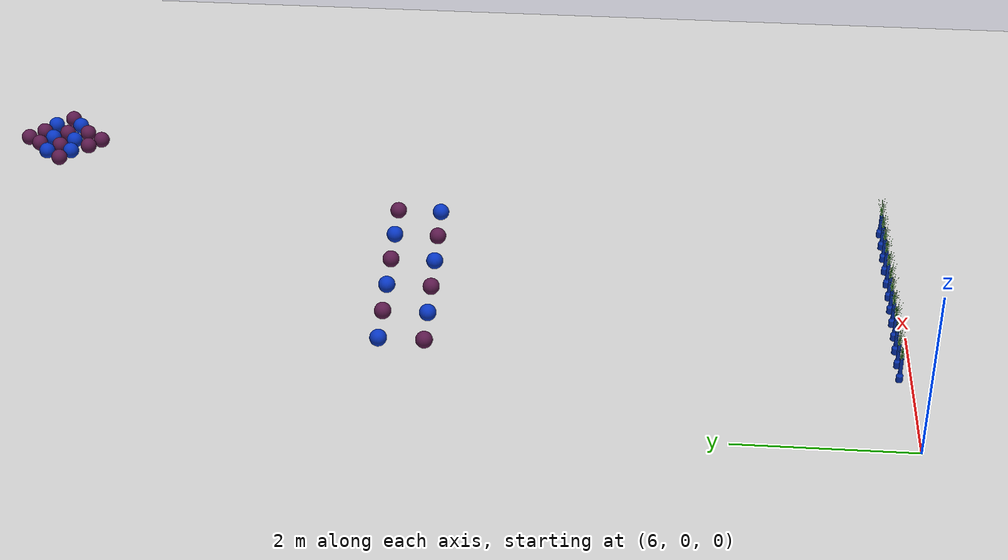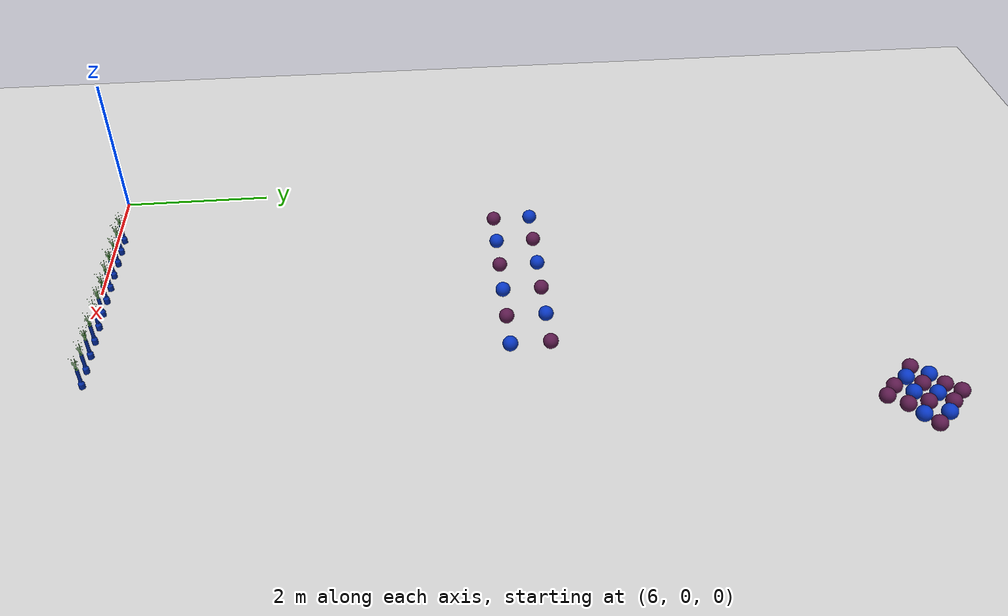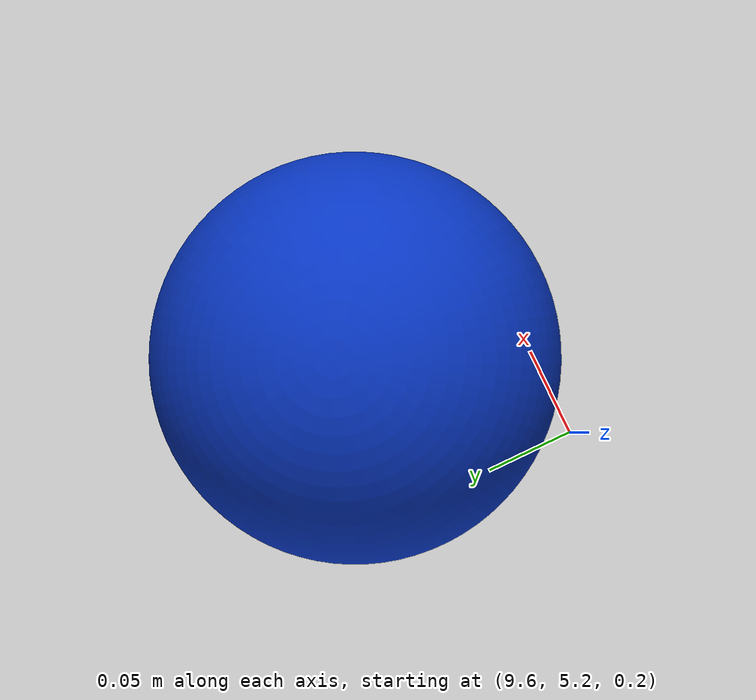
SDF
<sdf version="1.7">
 <world name="default">
  <light name="sun" type="directional">
   <pose>0 0 10 0 -0 0</pose>
   <diffuse>0.8 0.8 0.8 1</diffuse>
   <specular>0.2 0.2 0.2 1</specular>
   <attenuation>
    <range>1000</range>
    <constant>0.9</constant>
    <linear>0.01</linear>
    <quadratic>0.001</quadratic>
   </attenuation>
   <direction>-0.5 0.1 -0.9</direction>
   <spot><inner_angle>0</inner_angle><outer_angle>0</outer_angle><falloff>0</falloff></spot>
  </light>
  <model name="ground_plane">
   <static>1</static>
   <link name="link">
    <collision name="collision">
     <geometry><plane><normal>0 0 1</normal><size>100 100</size></plane></geometry>
     <surface>
      <contact><collide_bitmask>65535</collide_bitmask></contact>
      <friction><ode><mu>100</mu><mu2>50</mu2></ode></friction>
     </surface>
    </collision>
    <visual name="visual">
     <cast_shadows>0</cast_shadows>
     <geometry><plane><normal>0 0 1</normal><size>100 100</size></plane></geometry>
     <material>
      <script><uri>file://media/materials/scripts/gazebo.material</uri><name>Gazebo/Grey</name></script>
     </material>
    </visual>
   </link>
  </model>
  <gravity>0 0 -9.8</gravity>
  <magnetic_field>6e-06 2.3e-05 -4.2e-05</magnetic_field>
  <atmosphere type="adiabatic"/>
  <physics type="ode">
   <max_step_size>0.001</max_step_size>
   <real_time_factor>1</real_time_factor>
   <real_time_update_rate>1000</real_time_update_rate>
  </physics>
  <scene><ambient>0.4 0.4 0.4 1</ambient><background>0.7 0.7 0.7 1</background><shadows>1</shadows></scene>
  <audio><device>default</device></audio>
  <spherical_coordinates>
   <surface_model>EARTH_WGS84</surface_model>
   <latitude_deg>0</latitude_deg>
   <longitude_deg>0</longitude_deg>
   <elevation>0</elevation>
   <heading_deg>0</heading_deg>
  </spherical_coordinates>
  <model name="seed_blue">
   <link name="link_1">
    <inertial>
     <mass>1</mass>
     <inertia>
      <ixx>0.166667</ixx>
      <ixy>0</ixy>
      <ixz>0</ixz>
      <iyy>0.166667</iyy>
      <iyz>0</iyz>
      <izz>0.166667</izz>
     </inertia>
    </inertial>
    <visual name="visual">
     <geometry>
      <mesh>
       <uri>/home/entity014/abu2024_ws/src/abu_description/worlds/seed_blue.dae</uri>
       <scale>1 1 1</scale>
      </mesh>
     </geometry>
    </visual>
    <collision name="collision">
     <geometry>
      <mesh>
       <uri>/home/entity014/abu2024_ws/src/abu_description/worlds/seed_blue.dae</uri>
       <scale>1 1 1</scale>
      </mesh>
     </geometry>
     <surface>
      <friction>
       <ode><mu>1</mu><mu2>1</mu2><fdir1>0 0 0</fdir1><slip1>0</slip1><slip2>0</slip2></ode>
       <torsional>
        <coefficient>1</coefficient>
        <patch_radius>0</patch_radius>
        <surface_radius>0</surface_radius>
        <use_patch_radius>1</use_patch_radius>
        <ode><slip>0</slip></ode>
       </torsional>
      </friction>
      <bounce><restitution_coefficient>0</restitution_coefficient><threshold>1e+06</threshold></bounce>
      <contact>
       <collide_without_contact>0</collide_without_contact>
       <collide_without_contact_bitmask>1</collide_without_contact_bitmask>
       <collide_bitmask>1</collide_bitmask>
       <ode>
        <soft_cfm>0</soft_cfm>
        <soft_erp>0.2</soft_erp>
        <kp>1e+13</kp>
        <kd>1</kd>
        <max_vel>0.01</max_vel>
        <min_depth>0</min_depth>
       </ode>
       <bullet>
        <split_impulse>1</split_impulse>
        <split_impulse_penetration_threshold>-0.01</split_impulse_penetration_threshold>
        <soft_cfm>0</soft_cfm>
        <soft_erp>0.2</soft_erp>
        <kp>1e+13</kp>
        <kd>1</kd>
       </bullet>
      </contact>
     </surface>
    </collision>
   </link>
   <static>0</static>
   <pose>7.05811 0.163128 0.244369 6e-06 4e-06 0.000181</pose>
  </model>
  <model name="seed_blue_0">
   <link name="link_1">
    <inertial>
     <mass>1</mass>
     <inertia>
      <ixx>0.166667</ixx>
      <ixy>0</ixy>
      <ixz>0</ixz>
      <iyy>0.166667</iyy>
      <iyz>0</iyz>
      <izz>0.166667</izz>
     </inertia>
    </inertial>
    <visual name="visual">
     <geometry>
      <mesh>
       <uri>/home/entity014/abu2024_ws/src/abu_description/worlds/seed_blue.dae</uri>
       <scale>1 1 1</scale>
      </mesh>
     </geometry>
    </visual>
    <collision name="collision">
     <geometry>
      <mesh>
       <uri>/home/entity014/abu2024_ws/src/abu_description/worlds/seed_blue.dae</uri>
       <scale>1 1 1</scale>
      </mesh>
     </geometry>
     <surface>
      <friction>
       <ode><mu>1</mu><mu2>1</mu2><fdir1>0 0 0</fdir1><slip1>0</slip1><slip2>0</slip2></ode>
       <torsional>
        <coefficient>1</coefficient>
        <patch_radius>0</patch_radius>
        <surface_radius>0</surface_radius>
        <use_patch_radius>1</use_patch_radius>
        <ode><slip>0</slip></ode>
       </torsional>
      </friction>
      <bounce><restitution_coefficient>0</restitution_coefficient><threshold>1e+06</threshold></bounce>
      <contact>
       <collide_without_contact>0</collide_without_contact>
       <collide_without_contact_bitmask>1</collide_without_contact_bitmask>
       <collide_bitmask>1</collide_bitmask>
       <ode>
        <soft_cfm>0</soft_cfm>
        <soft_erp>0.2</soft_erp>
        <kp>1e+13</kp>
        <kd>1</kd>
        <max_vel>0.01</max_vel>
        <min_depth>0</min_depth>
       </ode>
       <bullet>
        <split_impulse>1</split_impulse>
        <split_impulse_penetration_threshold>-0.01</split_impulse_penetration_threshold>
        <soft_cfm>0</soft_cfm>
        <soft_erp>0.2</soft_erp>
        <kp>1e+13</kp>
        <kd>1</kd>
       </bullet>
      </contact>
     </surface>
    </collision>
   </link>
   <static>0</static>
   <pose>7.30361 0.167483 0.24437 1e-05 -1e-05 -0.016875</pose>
  </model>
  <model name="seed_blue_1">
   <link name="link_1">
    <inertial>
     <mass>1</mass>
     <inertia>
      <ixx>0.166667</ixx>
      <ixy>0</ixy>
      <ixz>0</ixz>
      <iyy>0.166667</iyy>
      <iyz>0</iyz>
      <izz>0.166667</izz>
     </inertia>
    </inertial>
    <visual name="visual">
     <geometry>
      <mesh>
       <uri>/home/entity014/abu2024_ws/src/abu_description/worlds/seed_blue.dae</uri>
       <scale>1 1 1</scale>
      </mesh>
     </geometry>
    </visual>
    <collision name="collision">
     <geometry>
      <mesh>
       <uri>/home/entity014/abu2024_ws/src/abu_description/worlds/seed_blue.dae</uri>
       <scale>1 1 1</scale>
      </mesh>
     </geometry>
     <surface>
      <friction>
       <ode><mu>1</mu><mu2>1</mu2><fdir1>0 0 0</fdir1><slip1>0</slip1><slip2>0</slip2></ode>
       <torsional>
        <coefficient>1</coefficient>
        <patch_radius>0</patch_radius>
        <surface_radius>0</surface_radius>
        <use_patch_radius>1</use_patch_radius>
        <ode><slip>0</slip></ode>
       </torsional>
      </friction>
      <bounce><restitution_coefficient>0</restitution_coefficient><threshold>1e+06</threshold></bounce>
      <contact>
       <collide_without_contact>0</collide_without_contact>
       <collide_without_contact_bitmask>1</collide_without_contact_bitmask>
       <collide_bitmask>1</collide_bitmask>
       <ode>
        <soft_cfm>0</soft_cfm>
        <soft_erp>0.2</soft_erp>
        <kp>1e+13</kp>
        <kd>1</kd>
        <max_vel>0.01</max_vel>
        <min_depth>0</min_depth>
       </ode>
       <bullet>
        <split_impulse>1</split_impulse>
        <split_impulse_penetration_threshold>-0.01</split_impulse_penetration_threshold>
        <soft_cfm>0</soft_cfm>
        <soft_erp>0.2</soft_erp>
        <kp>1e+13</kp>
        <kd>1</kd>
       </bullet>
      </contact>
     </surface>
    </collision>
   </link>
   <static>0</static>
   <pose>7.5539 0.168937 0.244369 -3e-06 2e-06 4.8e-05</pose>
  </model>
  <model name="seed_blue_2">
   <link name="link_1">
    <inertial>
     <mass>1</mass>
     <inertia>
      <ixx>0.166667</ixx>
      <ixy>0</ixy>
      <ixz>0</ixz>
      <iyy>0.166667</iyy>
      <iyz>0</iyz>
      <izz>0.166667</izz>
     </inertia>
    </inertial>
    <visual name="visual">
     <geometry>
      <mesh>
       <uri>/home/entity014/abu2024_ws/src/abu_description/worlds/seed_blue.dae</uri>
       <scale>1 1 1</scale>
      </mesh>
     </geometry>
    </visual>
    <collision name="collision">
     <geometry>
      <mesh>
       <uri>/home/entity014/abu2024_ws/src/abu_description/worlds/seed_blue.dae</uri>
       <scale>1 1 1</scale>
      </mesh>
     </geometry>
     <surface>
      <friction>
       <ode><mu>1</mu><mu2>1</mu2><fdir1>0 0 0</fdir1><slip1>0</slip1><slip2>0</slip2></ode>
       <torsional>
        <coefficient>1</coefficient>
        <patch_radius>0</patch_radius>
        <surface_radius>0</surface_radius>
        <use_patch_radius>1</use_patch_radius>
        <ode><slip>0</slip></ode>
       </torsional>
      </friction>
      <bounce><restitution_coefficient>0</restitution_coefficient><threshold>1e+06</threshold></bounce>
      <contact>
       <collide_without_contact>0</collide_without_contact>
       <collide_without_contact_bitmask>1</collide_without_contact_bitmask>
       <collide_bitmask>1</collide_bitmask>
       <ode>
        <soft_cfm>0</soft_cfm>
        <soft_erp>0.2</soft_erp>
        <kp>1e+13</kp>
        <kd>1</kd>
        <max_vel>0.01</max_vel>
        <min_depth>0</min_depth>
       </ode>
       <bullet>
        <split_impulse>1</split_impulse>
        <split_impulse_penetration_threshold>-0.01</split_impulse_penetration_threshold>
        <soft_cfm>0</soft_cfm>
        <soft_erp>0.2</soft_erp>
        <kp>1e+13</kp>
        <kd>1</kd>
       </bullet>
      </contact>
     </surface>
    </collision>
   </link>
   <static>0</static>
   <pose>7.80373 0.163084 0.244369 4e-06 1e-06 -6.5e-05</pose>
  </model>
  <model name="seed_blue_3">
   <link name="link_1">
    <inertial>
     <mass>1</mass>
     <inertia>
      <ixx>0.166667</ixx>
      <ixy>0</ixy>
      <ixz>0</ixz>
      <iyy>0.166667</iyy>
      <iyz>0</iyz>
      <izz>0.166667</izz>
     </inertia>
    </inertial>
    <visual name="visual">
     <geometry>
      <mesh>
       <uri>/home/entity014/abu2024_ws/src/abu_description/worlds/seed_blue.dae</uri>
       <scale>1 1 1</scale>
      </mesh>
     </geometry>
    </visual>
    <collision name="collision">
     <geometry>
      <mesh>
       <uri>/home/entity014/abu2024_ws/src/abu_description/worlds/seed_blue.dae</uri>
       <scale>1 1 1</scale>
      </mesh>
     </geometry>
     <surface>
      <friction>
       <ode><mu>1</mu><mu2>1</mu2><fdir1>0 0 0</fdir1><slip1>0</slip1><slip2>0</slip2></ode>
       <torsional>
        <coefficient>1</coefficient>
        <patch_radius>0</patch_radius>
        <surface_radius>0</surface_radius>
        <use_patch_radius>1</use_patch_radius>
        <ode><slip>0</slip></ode>
       </torsional>
      </friction>
      <bounce><restitution_coefficient>0</restitution_coefficient><threshold>1e+06</threshold></bounce>
      <contact>
       <collide_without_contact>0</collide_without_contact>
       <collide_without_contact_bitmask>1</collide_without_contact_bitmask>
       <collide_bitmask>1</collide_bitmask>
       <ode>
        <soft_cfm>0</soft_cfm>
        <soft_erp>0.2</soft_erp>
        <kp>1e+13</kp>
        <kd>1</kd>
        <max_vel>0.01</max_vel>
        <min_depth>0</min_depth>
       </ode>
       <bullet>
        <split_impulse>1</split_impulse>
        <split_impulse_penetration_threshold>-0.01</split_impulse_penetration_threshold>
        <soft_cfm>0</soft_cfm>
        <soft_erp>0.2</soft_erp>
        <kp>1e+13</kp>
        <kd>1</kd>
       </bullet>
      </contact>
     </surface>
    </collision>
   </link>
   <static>0</static>
   <pose>8.05521 0.164025 0.244369 2e-06 -8e-06 7.7e-05</pose>
  </model>
  <model name="seed_blue_4">
   <link name="link_1">
    <inertial>
     <mass>1</mass>
     <inertia>
      <ixx>0.166667</ixx>
      <ixy>0</ixy>
      <ixz>0</ixz>
      <iyy>0.166667</iyy>
      <iyz>0</iyz>
      <izz>0.166667</izz>
     </inertia>
    </inertial>
    <visual name="visual">
     <geometry>
      <mesh>
       <uri>/home/entity014/abu2024_ws/src/abu_description/worlds/seed_blue.dae</uri>
       <scale>1 1 1</scale>
      </mesh>
     </geometry>
    </visual>
    <collision name="collision">
     <geometry>
      <mesh>
       <uri>/home/entity014/abu2024_ws/src/abu_description/worlds/seed_blue.dae</uri>
       <scale>1 1 1</scale>
      </mesh>
     </geometry>
     <surface>
      <friction>
       <ode><mu>1</mu><mu2>1</mu2><fdir1>0 0 0</fdir1><slip1>0</slip1><slip2>0</slip2></ode>
       <torsional>
        <coefficient>1</coefficient>
        <patch_radius>0</patch_radius>
        <surface_radius>0</surface_radius>
        <use_patch_radius>1</use_patch_radius>
        <ode><slip>0</slip></ode>
       </torsional>
      </friction>
      <bounce><restitution_coefficient>0</restitution_coefficient><threshold>1e+06</threshold></bounce>
      <contact>
       <collide_without_contact>0</collide_without_contact>
       <collide_without_contact_bitmask>1</collide_without_contact_bitmask>
       <collide_bitmask>1</collide_bitmask>
       <ode>
        <soft_cfm>0</soft_cfm>
        <soft_erp>0.2</soft_erp>
        <kp>1e+13</kp>
        <kd>1</kd>
        <max_vel>0.01</max_vel>
        <min_depth>0</min_depth>
       </ode>
       <bullet>
        <split_impulse>1</split_impulse>
        <split_impulse_penetration_threshold>-0.01</split_impulse_penetration_threshold>
        <soft_cfm>0</soft_cfm>
        <soft_erp>0.2</soft_erp>
        <kp>1e+13</kp>
        <kd>1</kd>
       </bullet>
      </contact>
     </surface>
    </collision>
   </link>
   <static>0</static>
   <pose>8.30615 0.165431 0.24437 -4e-06 -1.2e-05 -0.000523</pose>
  </model>
  <model name="seed_blue_5">
   <link name="link_1">
    <inertial>
     <mass>1</mass>
     <inertia>
      <ixx>0.166667</ixx>
      <ixy>0</ixy>
      <ixz>0</ixz>
      <iyy>0.166667</iyy>
      <iyz>0</iyz>
      <izz>0.166667</izz>
     </inertia>
    </inertial>
    <visual name="visual">
     <geometry>
      <mesh>
       <uri>/home/entity014/abu2024_ws/src/abu_description/worlds/seed_blue.dae</uri>
       <scale>1 1 1</scale>
      </mesh>
     </geometry>
    </visual>
    <collision name="collision">
     <geometry>
      <mesh>
       <uri>/home/entity014/abu2024_ws/src/abu_description/worlds/seed_blue.dae</uri>
       <scale>1 1 1</scale>
      </mesh>
     </geometry>
     <surface>
      <friction>
       <ode><mu>1</mu><mu2>1</mu2><fdir1>0 0 0</fdir1><slip1>0</slip1><slip2>0</slip2></ode>
       <torsional>
        <coefficient>1</coefficient>
        <patch_radius>0</patch_radius>
        <surface_radius>0</surface_radius>
        <use_patch_radius>1</use_patch_radius>
        <ode><slip>0</slip></ode>
       </torsional>
      </friction>
      <bounce><restitution_coefficient>0</restitution_coefficient><threshold>1e+06</threshold></bounce>
      <contact>
       <collide_without_contact>0</collide_without_contact>
       <collide_without_contact_bitmask>1</collide_without_contact_bitmask>
       <collide_bitmask>1</collide_bitmask>
       <ode>
        <soft_cfm>0</soft_cfm>
        <soft_erp>0.2</soft_erp>
        <kp>1e+13</kp>
        <kd>1</kd>
        <max_vel>0.01</max_vel>
        <min_depth>0</min_depth>
       </ode>
       <bullet>
        <split_impulse>1</split_impulse>
        <split_impulse_penetration_threshold>-0.01</split_impulse_penetration_threshold>
        <soft_cfm>0</soft_cfm>
        <soft_erp>0.2</soft_erp>
        <kp>1e+13</kp>
        <kd>1</kd>
       </bullet>
      </contact>
     </surface>
    </collision>
   </link>
   <static>0</static>
   <pose>8.5531 0.164074 0.244369 -9e-06 3e-06 6.8e-05</pose>
  </model>
  <model name="seed_blue_6">
   <link name="link_1">
    <inertial>
     <mass>1</mass>
     <inertia>
      <ixx>0.166667</ixx>
      <ixy>0</ixy>
      <ixz>0</ixz>
      <iyy>0.166667</iyy>
      <iyz>0</iyz>
      <izz>0.166667</izz>
     </inertia>
    </inertial>
    <visual name="visual">
     <geometry>
      <mesh>
       <uri>/home/entity014/abu2024_ws/src/abu_description/worlds/seed_blue.dae</uri>
       <scale>1 1 1</scale>
      </mesh>
     </geometry>
    </visual>
    <collision name="collision">
     <geometry>
      <mesh>
       <uri>/home/entity014/abu2024_ws/src/abu_description/worlds/seed_blue.dae</uri>
       <scale>1 1 1</scale>
      </mesh>
     </geometry>
     <surface>
      <friction>
       <ode><mu>1</mu><mu2>1</mu2><fdir1>0 0 0</fdir1><slip1>0</slip1><slip2>0</slip2></ode>
       <torsional>
        <coefficient>1</coefficient>
        <patch_radius>0</patch_radius>
        <surface_radius>0</surface_radius>
        <use_patch_radius>1</use_patch_radius>
        <ode><slip>0</slip></ode>
       </torsional>
      </friction>
      <bounce><restitution_coefficient>0</restitution_coefficient><threshold>1e+06</threshold></bounce>
      <contact>
       <collide_without_contact>0</collide_without_contact>
       <collide_without_contact_bitmask>1</collide_without_contact_bitmask>
       <collide_bitmask>1</collide_bitmask>
       <ode>
        <soft_cfm>0</soft_cfm>
        <soft_erp>0.2</soft_erp>
        <kp>1e+13</kp>
        <kd>1</kd>
        <max_vel>0.01</max_vel>
        <min_depth>0</min_depth>
       </ode>
       <bullet>
        <split_impulse>1</split_impulse>
        <split_impulse_penetration_threshold>-0.01</split_impulse_penetration_threshold>
        <soft_cfm>0</soft_cfm>
        <soft_erp>0.2</soft_erp>
        <kp>1e+13</kp>
        <kd>1</kd>
       </bullet>
      </contact>
     </surface>
    </collision>
   </link>
   <static>0</static>
   <pose>8.80363 0.166132 0.24437 -1e-05 1.1e-05 0.000953</pose>
  </model>
  <model name="seed_blue_7">
   <link name="link_1">
    <inertial>
     <mass>1</mass>
     <inertia>
      <ixx>0.166667</ixx>
      <ixy>0</ixy>
      <ixz>0</ixz>
      <iyy>0.166667</iyy>
      <iyz>0</iyz>
      <izz>0.166667</izz>
     </inertia>
    </inertial>
    <visual name="visual">
     <geometry>
      <mesh>
       <uri>/home/entity014/abu2024_ws/src/abu_description/worlds/seed_blue.dae</uri>
       <scale>1 1 1</scale>
      </mesh>
     </geometry>
    </visual>
    <collision name="collision">
     <geometry>
      <mesh>
       <uri>/home/entity014/abu2024_ws/src/abu_description/worlds/seed_blue.dae</uri>
       <scale>1 1 1</scale>
      </mesh>
     </geometry>
     <surface>
      <friction>
       <ode><mu>1</mu><mu2>1</mu2><fdir1>0 0 0</fdir1><slip1>0</slip1><slip2>0</slip2></ode>
       <torsional>
        <coefficient>1</coefficient>
        <patch_radius>0</patch_radius>
        <surface_radius>0</surface_radius>
        <use_patch_radius>1</use_patch_radius>
        <ode><slip>0</slip></ode>
       </torsional>
      </friction>
      <bounce><restitution_coefficient>0</restitution_coefficient><threshold>1e+06</threshold></bounce>
      <contact>
       <collide_without_contact>0</collide_without_contact>
       <collide_without_contact_bitmask>1</collide_without_contact_bitmask>
       <collide_bitmask>1</collide_bitmask>
       <ode>
        <soft_cfm>0</soft_cfm>
        <soft_erp>0.2</soft_erp>
        <kp>1e+13</kp>
        <kd>1</kd>
        <max_vel>0.01</max_vel>
        <min_depth>0</min_depth>
       </ode>
       <bullet>
        <split_impulse>1</split_impulse>
        <split_impulse_penetration_threshold>-0.01</split_impulse_penetration_threshold>
        <soft_cfm>0</soft_cfm>
        <soft_erp>0.2</soft_erp>
        <kp>1e+13</kp>
        <kd>1</kd>
       </bullet>
      </contact>
     </surface>
    </collision>
   </link>
   <static>0</static>
   <pose>9.05932 0.167278 0.24436 1e-06 -6e-06 -0.000183</pose>
  </model>
  <model name="seed_blue_8">
   <link name="link_1">
    <inertial>
     <mass>1</mass>
     <inertia>
      <ixx>0.166667</ixx>
      <ixy>0</ixy>
      <ixz>0</ixz>
      <iyy>0.166667</iyy>
      <iyz>0</iyz>
      <izz>0.166667</izz>
     </inertia>
    </inertial>
    <visual name="visual">
     <geometry>
      <mesh>
       <uri>/home/entity014/abu2024_ws/src/abu_description/worlds/seed_blue.dae</uri>
       <scale>1 1 1</scale>
      </mesh>
     </geometry>
    </visual>
    <collision name="collision">
     <geometry>
      <mesh>
       <uri>/home/entity014/abu2024_ws/src/abu_description/worlds/seed_blue.dae</uri>
       <scale>1 1 1</scale>
      </mesh>
     </geometry>
     <surface>
      <friction>
       <ode><mu>1</mu><mu2>1</mu2><fdir1>0 0 0</fdir1><slip1>0</slip1><slip2>0</slip2></ode>
       <torsional>
        <coefficient>1</coefficient>
        <patch_radius>0</patch_radius>
        <surface_radius>0</surface_radius>
        <use_patch_radius>1</use_patch_radius>
        <ode><slip>0</slip></ode>
       </torsional>
      </friction>
      <bounce><restitution_coefficient>0</restitution_coefficient><threshold>1e+06</threshold></bounce>
      <contact>
       <collide_without_contact>0</collide_without_contact>
       <collide_without_contact_bitmask>1</collide_without_contact_bitmask>
       <collide_bitmask>1</collide_bitmask>
       <ode>
        <soft_cfm>0</soft_cfm>
        <soft_erp>0.2</soft_erp>
        <kp>1e+13</kp>
        <kd>1</kd>
        <max_vel>0.01</max_vel>
        <min_depth>0</min_depth>
       </ode>
       <bullet>
        <split_impulse>1</split_impulse>
        <split_impulse_penetration_threshold>-0.01</split_impulse_penetration_threshold>
        <soft_cfm>0</soft_cfm>
        <soft_erp>0.2</soft_erp>
        <kp>1e+13</kp>
        <kd>1</kd>
       </bullet>
      </contact>
     </surface>
    </collision>
   </link>
   <static>0</static>
   <pose>9.31235 0.166827 0.24436 5e-06 1.4e-05 0.000116</pose>
  </model>
  <model name="seed_blue_9">
   <link name="link_1">
    <inertial>
     <mass>1</mass>
     <inertia>
      <ixx>0.166667</ixx>
      <ixy>0</ixy>
      <ixz>0</ixz>
      <iyy>0.166667</iyy>
      <iyz>0</iyz>
      <izz>0.166667</izz>
     </inertia>
    </inertial>
    <visual name="visual">
     <geometry>
      <mesh>
       <uri>/home/entity014/abu2024_ws/src/abu_description/worlds/seed_blue.dae</uri>
       <scale>1 1 1</scale>
      </mesh>
     </geometry>
    </visual>
    <collision name="collision">
     <geometry>
      <mesh>
       <uri>/home/entity014/abu2024_ws/src/abu_description/worlds/seed_blue.dae</uri>
       <scale>1 1 1</scale>
      </mesh>
     </geometry>
     <surface>
      <friction>
       <ode><mu>1</mu><mu2>1</mu2><fdir1>0 0 0</fdir1><slip1>0</slip1><slip2>0</slip2></ode>
       <torsional>
        <coefficient>1</coefficient>
        <patch_radius>0</patch_radius>
        <surface_radius>0</surface_radius>
        <use_patch_radius>1</use_patch_radius>
        <ode><slip>0</slip></ode>
       </torsional>
      </friction>
      <bounce><restitution_coefficient>0</restitution_coefficient><threshold>1e+06</threshold></bounce>
      <contact>
       <collide_without_contact>0</collide_without_contact>
       <collide_without_contact_bitmask>1</collide_without_contact_bitmask>
       <collide_bitmask>1</collide_bitmask>
       <ode>
        <soft_cfm>0</soft_cfm>
        <soft_erp>0.2</soft_erp>
        <kp>1e+13</kp>
        <kd>1</kd>
        <max_vel>0.01</max_vel>
        <min_depth>0</min_depth>
       </ode>
       <bullet>
        <split_impulse>1</split_impulse>
        <split_impulse_penetration_threshold>-0.01</split_impulse_penetration_threshold>
        <soft_cfm>0</soft_cfm>
        <soft_erp>0.2</soft_erp>
        <kp>1e+13</kp>
        <kd>1</kd>
       </bullet>
      </contact>
     </surface>
    </collision>
   </link>
   <static>0</static>
   <pose>9.56235 0.167683 0.244369 -0 -6e-06 -0.00027</pose>
  </model>
  <model name="seed_blue_10">
   <link name="link_1">
    <inertial>
     <mass>1</mass>
     <inertia>
      <ixx>0.166667</ixx>
      <ixy>0</ixy>
      <ixz>0</ixz>
      <iyy>0.166667</iyy>
      <iyz>0</iyz>
      <izz>0.166667</izz>
     </inertia>
    </inertial>
    <visual name="visual">
     <geometry>
      <mesh>
       <uri>/home/entity014/abu2024_ws/src/abu_description/worlds/seed_blue.dae</uri>
       <scale>1 1 1</scale>
      </mesh>
     </geometry>
    </visual>
    <collision name="collision">
     <geometry>
      <mesh>
       <uri>/home/entity014/abu2024_ws/src/abu_description/worlds/seed_blue.dae</uri>
       <scale>1 1 1</scale>
      </mesh>
     </geometry>
     <surface>
      <friction>
       <ode><mu>1</mu><mu2>1</mu2><fdir1>0 0 0</fdir1><slip1>0</slip1><slip2>0</slip2></ode>
       <torsional>
        <coefficient>1</coefficient>
        <patch_radius>0</patch_radius>
        <surface_radius>0</surface_radius>
        <use_patch_radius>1</use_patch_radius>
        <ode><slip>0</slip></ode>
       </torsional>
      </friction>
      <bounce><restitution_coefficient>0</restitution_coefficient><threshold>1e+06</threshold></bounce>
      <contact>
       <collide_without_contact>0</collide_without_contact>
       <collide_without_contact_bitmask>1</collide_without_contact_bitmask>
       <collide_bitmask>1</collide_bitmask>
       <ode>
        <soft_cfm>0</soft_cfm>
        <soft_erp>0.2</soft_erp>
        <kp>1e+13</kp>
        <kd>1</kd>
        <max_vel>0.01</max_vel>
        <min_depth>0</min_depth>
       </ode>
       <bullet>
        <split_impulse>1</split_impulse>
        <split_impulse_penetration_threshold>-0.01</split_impulse_penetration_threshold>
        <soft_cfm>0</soft_cfm>
        <soft_erp>0.2</soft_erp>
        <kp>1e+13</kp>
        <kd>1</kd>
       </bullet>
      </contact>
     </surface>
    </collision>
   </link>
   <static>0</static>
   <pose>9.81184 0.168238 0.24436 2e-06 -8e-06 -8.2e-05</pose>
  </model>
  <model name="ball_empty_clone_4">
   <link name="link_1">
    <inertial>
     <mass>1</mass>
     <inertia>
      <ixx>0.166667</ixx>
      <ixy>0</ixy>
      <ixz>0</ixz>
      <iyy>0.166667</iyy>
      <iyz>0</iyz>
      <izz>0.166667</izz>
     </inertia>
    </inertial>
    <visual name="visual">
     <geometry>
      <mesh>
       <uri>/home/entity014/abu2024_ws/src/abu_description/worlds/ball_empty.dae</uri>
       <scale>1 1 1</scale>
      </mesh>
     </geometry>
    </visual>
    <collision name="collision">
     <geometry>
      <mesh>
       <uri>/home/entity014/abu2024_ws/src/abu_description/worlds/ball_empty.dae</uri>
       <scale>1 1 1</scale>
      </mesh>
     </geometry>
     <surface>
      <friction>
       <ode><mu>1</mu><mu2>1</mu2><fdir1>0 0 0</fdir1><slip1>0</slip1><slip2>0</slip2></ode>
       <torsional>
        <coefficient>1</coefficient>
        <patch_radius>0</patch_radius>
        <surface_radius>0</surface_radius>
        <use_patch_radius>1</use_patch_radius>
        <ode><slip>0</slip></ode>
       </torsional>
      </friction>
      <bounce><restitution_coefficient>0</restitution_coefficient><threshold>1e+06</threshold></bounce>
      <contact>
       <collide_without_contact>0</collide_without_contact>
       <collide_without_contact_bitmask>1</collide_without_contact_bitmask>
       <collide_bitmask>1</collide_bitmask>
       <ode>
        <soft_cfm>0</soft_cfm>
        <soft_erp>0.2</soft_erp>
        <kp>1e+13</kp>
        <kd>1</kd>
        <max_vel>0.01</max_vel>
        <min_depth>0</min_depth>
       </ode>
       <bullet>
        <split_impulse>1</split_impulse>
        <split_impulse_penetration_threshold>-0.01</split_impulse_penetration_threshold>
        <soft_cfm>0</soft_cfm>
        <soft_erp>0.2</soft_erp>
        <kp>1e+13</kp>
        <kd>1</kd>
       </bullet>
      </contact>
     </surface>
    </collision>
   </link>
   <static>0</static>
   <pose>7.18303 5.29135 0.302532 -0.308724 -0.324747 0.220938</pose>
  </model>
  <model name="ball_empty_clone_5">
   <link name="link_1">
    <inertial>
     <mass>1</mass>
     <inertia>
      <ixx>0.166667</ixx>
      <ixy>0</ixy>
      <ixz>0</ixz>
      <iyy>0.166667</iyy>
      <iyz>0</iyz>
      <izz>0.166667</izz>
     </inertia>
    </inertial>
    <visual name="visual">
     <geometry>
      <mesh>
       <uri>/home/entity014/abu2024_ws/src/abu_description/worlds/ball_empty.dae</uri>
       <scale>1 1 1</scale>
      </mesh>
     </geometry>
    </visual>
    <collision name="collision">
     <geometry>
      <mesh>
       <uri>/home/entity014/abu2024_ws/src/abu_description/worlds/ball_empty.dae</uri>
       <scale>1 1 1</scale>
      </mesh>
     </geometry>
     <surface>
      <friction>
       <ode><mu>1</mu><mu2>1</mu2><fdir1>0 0 0</fdir1><slip1>0</slip1><slip2>0</slip2></ode>
       <torsional>
        <coefficient>1</coefficient>
        <patch_radius>0</patch_radius>
        <surface_radius>0</surface_radius>
        <use_patch_radius>1</use_patch_radius>
        <ode><slip>0</slip></ode>
       </torsional>
      </friction>
      <bounce><restitution_coefficient>0</restitution_coefficient><threshold>1e+06</threshold></bounce>
      <contact>
       <collide_without_contact>0</collide_without_contact>
       <collide_without_contact_bitmask>1</collide_without_contact_bitmask>
       <collide_bitmask>1</collide_bitmask>
       <ode>
        <soft_cfm>0</soft_cfm>
        <soft_erp>0.2</soft_erp>
        <kp>1e+13</kp>
        <kd>1</kd>
        <max_vel>0.01</max_vel>
        <min_depth>0</min_depth>
       </ode>
       <bullet>
        <split_impulse>1</split_impulse>
        <split_impulse_penetration_threshold>-0.01</split_impulse_penetration_threshold>
        <soft_cfm>0</soft_cfm>
        <soft_erp>0.2</soft_erp>
        <kp>1e+13</kp>
        <kd>1</kd>
       </bullet>
      </contact>
     </surface>
    </collision>
   </link>
   <static>0</static>
   <pose>7.68235 5.79116 0.302543 -0.10185 -0.065181 -0.133237</pose>
  </model>
  <model name="ball_empty_clone_6">
   <link name="link_1">
    <inertial>
     <mass>1</mass>
     <inertia>
      <ixx>0.166667</ixx>
      <ixy>0</ixy>
      <ixz>0</ixz>
      <iyy>0.166667</iyy>
      <iyz>0</iyz>
      <izz>0.166667</izz>
     </inertia>
    </inertial>
    <visual name="visual">
     <geometry>
      <mesh>
       <uri>/home/entity014/abu2024_ws/src/abu_description/worlds/ball_empty.dae</uri>
       <scale>1 1 1</scale>
      </mesh>
     </geometry>
    </visual>
    <collision name="collision">
     <geometry>
      <mesh>
       <uri>/home/entity014/abu2024_ws/src/abu_description/worlds/ball_empty.dae</uri>
       <scale>1 1 1</scale>
      </mesh>
     </geometry>
     <surface>
      <friction>
       <ode><mu>1</mu><mu2>1</mu2><fdir1>0 0 0</fdir1><slip1>0</slip1><slip2>0</slip2></ode>
       <torsional>
        <coefficient>1</coefficient>
        <patch_radius>0</patch_radius>
        <surface_radius>0</surface_radius>
        <use_patch_radius>1</use_patch_radius>
        <ode><slip>0</slip></ode>
       </torsional>
      </friction>
      <bounce><restitution_coefficient>0</restitution_coefficient><threshold>1e+06</threshold></bounce>
      <contact>
       <collide_without_contact>0</collide_without_contact>
       <collide_without_contact_bitmask>1</collide_without_contact_bitmask>
       <collide_bitmask>1</collide_bitmask>
       <ode>
        <soft_cfm>0</soft_cfm>
        <soft_erp>0.2</soft_erp>
        <kp>1e+13</kp>
        <kd>1</kd>
        <max_vel>0.01</max_vel>
        <min_depth>0</min_depth>
       </ode>
       <bullet>
        <split_impulse>1</split_impulse>
        <split_impulse_penetration_threshold>-0.01</split_impulse_penetration_threshold>
        <soft_cfm>0</soft_cfm>
        <soft_erp>0.2</soft_erp>
        <kp>1e+13</kp>
        <kd>1</kd>
       </bullet>
      </contact>
     </surface>
    </collision>
   </link>
   <static>0</static>
   <pose>8.18146 5.29249 0.302558 -0.04216 -0.10908 0.102511</pose>
  </model>
  <model name="ball_empty_clone_7">
   <link name="link_1">
    <inertial>
     <mass>1</mass>
     <inertia>
      <ixx>0.166667</ixx>
      <ixy>0</ixy>
      <ixz>0</ixz>
      <iyy>0.166667</iyy>
      <iyz>0</iyz>
      <izz>0.166667</izz>
     </inertia>
    </inertial>
    <visual name="visual">
     <geometry>
      <mesh>
       <uri>/home/entity014/abu2024_ws/src/abu_description/worlds/ball_empty.dae</uri>
       <scale>1 1 1</scale>
      </mesh>
     </geometry>
    </visual>
    <collision name="collision">
     <geometry>
      <mesh>
       <uri>/home/entity014/abu2024_ws/src/abu_description/worlds/ball_empty.dae</uri>
       <scale>1 1 1</scale>
      </mesh>
     </geometry>
     <surface>
      <friction>
       <ode><mu>1</mu><mu2>1</mu2><fdir1>0 0 0</fdir1><slip1>0</slip1><slip2>0</slip2></ode>
       <torsional>
        <coefficient>1</coefficient>
        <patch_radius>0</patch_radius>
        <surface_radius>0</surface_radius>
        <use_patch_radius>1</use_patch_radius>
        <ode><slip>0</slip></ode>
       </torsional>
      </friction>
      <bounce><restitution_coefficient>0</restitution_coefficient><threshold>1e+06</threshold></bounce>
      <contact>
       <collide_without_contact>0</collide_without_contact>
       <collide_without_contact_bitmask>1</collide_without_contact_bitmask>
       <collide_bitmask>1</collide_bitmask>
       <ode>
        <soft_cfm>0</soft_cfm>
        <soft_erp>0.2</soft_erp>
        <kp>1e+13</kp>
        <kd>1</kd>
        <max_vel>0.01</max_vel>
        <min_depth>0</min_depth>
       </ode>
       <bullet>
        <split_impulse>1</split_impulse>
        <split_impulse_penetration_threshold>-0.01</split_impulse_penetration_threshold>
        <soft_cfm>0</soft_cfm>
        <soft_erp>0.2</soft_erp>
        <kp>1e+13</kp>
        <kd>1</kd>
       </bullet>
      </contact>
     </surface>
    </collision>
   </link>
   <static>0</static>
   <pose>8.68242 5.79102 0.302581 -0.210915 0.0334 -0.073544</pose>
  </model>
  <model name="ball_empty_clone_8">
   <link name="link_1">
    <inertial>
     <mass>1</mass>
     <inertia>
      <ixx>0.166667</ixx>
      <ixy>0</ixy>
      <ixz>0</ixz>
      <iyy>0.166667</iyy>
      <iyz>0</iyz>
      <izz>0.166667</izz>
     </inertia>
    </inertial>
    <visual name="visual">
     <geometry>
      <mesh>
       <uri>/home/entity014/abu2024_ws/src/abu_description/worlds/ball_empty.dae</uri>
       <scale>1 1 1</scale>
      </mesh>
     </geometry>
    </visual>
    <collision name="collision">
     <geometry>
      <mesh>
       <uri>/home/entity014/abu2024_ws/src/abu_description/worlds/ball_empty.dae</uri>
       <scale>1 1 1</scale>
      </mesh>
     </geometry>
     <surface>
      <friction>
       <ode><mu>1</mu><mu2>1</mu2><fdir1>0 0 0</fdir1><slip1>0</slip1><slip2>0</slip2></ode>
       <torsional>
        <coefficient>1</coefficient>
        <patch_radius>0</patch_radius>
        <surface_radius>0</surface_radius>
        <use_patch_radius>1</use_patch_radius>
        <ode><slip>0</slip></ode>
       </torsional>
      </friction>
      <bounce><restitution_coefficient>0</restitution_coefficient><threshold>1e+06</threshold></bounce>
      <contact>
       <collide_without_contact>0</collide_without_contact>
       <collide_without_contact_bitmask>1</collide_without_contact_bitmask>
       <collide_bitmask>1</collide_bitmask>
       <ode>
        <soft_cfm>0</soft_cfm>
        <soft_erp>0.2</soft_erp>
        <kp>1e+13</kp>
        <kd>1</kd>
        <max_vel>0.01</max_vel>
        <min_depth>0</min_depth>
       </ode>
       <bullet>
        <split_impulse>1</split_impulse>
        <split_impulse_penetration_threshold>-0.01</split_impulse_penetration_threshold>
        <soft_cfm>0</soft_cfm>
        <soft_erp>0.2</soft_erp>
        <kp>1e+13</kp>
        <kd>1</kd>
       </bullet>
      </contact>
     </surface>
    </collision>
   </link>
   <static>0</static>
   <pose>9.18388 5.29333 0.302566 0.273809 0.017133 0.024336</pose>
  </model>
  <model name="ball_empty_clone_9">
   <link name="link_1">
    <inertial>
     <mass>1</mass>
     <inertia>
      <ixx>0.166667</ixx>
      <ixy>0</ixy>
      <ixz>0</ixz>
      <iyy>0.166667</iyy>
      <iyz>0</iyz>
      <izz>0.166667</izz>
     </inertia>
    </inertial>
    <visual name="visual">
     <geometry>
      <mesh>
       <uri>/home/entity014/abu2024_ws/src/abu_description/worlds/ball_empty.dae</uri>
       <scale>1 1 1</scale>
      </mesh>
     </geometry>
    </visual>
    <collision name="collision">
     <geometry>
      <mesh>
       <uri>/home/entity014/abu2024_ws/src/abu_description/worlds/ball_empty.dae</uri>
       <scale>1 1 1</scale>
      </mesh>
     </geometry>
     <surface>
      <friction>
       <ode><mu>1</mu><mu2>1</mu2><fdir1>0 0 0</fdir1><slip1>0</slip1><slip2>0</slip2></ode>
       <torsional>
        <coefficient>1</coefficient>
        <patch_radius>0</patch_radius>
        <surface_radius>0</surface_radius>
        <use_patch_radius>1</use_patch_radius>
        <ode><slip>0</slip></ode>
       </torsional>
      </friction>
      <bounce><restitution_coefficient>0</restitution_coefficient><threshold>1e+06</threshold></bounce>
      <contact>
       <collide_without_contact>0</collide_without_contact>
       <collide_without_contact_bitmask>1</collide_without_contact_bitmask>
       <collide_bitmask>1</collide_bitmask>
       <ode>
        <soft_cfm>0</soft_cfm>
        <soft_erp>0.2</soft_erp>
        <kp>1e+13</kp>
        <kd>1</kd>
        <max_vel>0.01</max_vel>
        <min_depth>0</min_depth>
       </ode>
       <bullet>
        <split_impulse>1</split_impulse>
        <split_impulse_penetration_threshold>-0.01</split_impulse_penetration_threshold>
        <soft_cfm>0</soft_cfm>
        <soft_erp>0.2</soft_erp>
        <kp>1e+13</kp>
        <kd>1</kd>
       </bullet>
      </contact>
     </surface>
    </collision>
   </link>
   <static>0</static>
   <pose>9.68167 5.79272 0.302541 -0.15648 0.3284 -0.083313</pose>
  </model>
  <model name="ball_blue">
   <link name="link_1">
    <inertial>
     <mass>1</mass>
     <inertia>
      <ixx>0.166667</ixx>
      <ixy>0</ixy>
      <ixz>0</ixz>
      <iyy>0.166667</iyy>
      <iyz>0</iyz>
      <izz>0.166667</izz>
     </inertia>
    </inertial>
    <visual name="visual">
     <geometry>
      <mesh>
       <uri>/home/entity014/abu2024_ws/src/abu_description/worlds/ball_blue.dae</uri>
       <scale>1 1 1</scale>
      </mesh>
     </geometry>
    </visual>
    <collision name="collision">
     <geometry>
      <mesh>
       <uri>/home/entity014/abu2024_ws/src/abu_description/worlds/ball_blue.dae</uri>
       <scale>1 1 1</scale>
      </mesh>
     </geometry>
     <surface>
      <friction>
       <ode><mu>1</mu><mu2>1</mu2><fdir1>0 0 0</fdir1><slip1>0</slip1><slip2>0</slip2></ode>
       <torsional>
        <coefficient>1</coefficient>
        <patch_radius>0</patch_radius>
        <surface_radius>0</surface_radius>
        <use_patch_radius>1</use_patch_radius>
        <ode><slip>0</slip></ode>
       </torsional>
      </friction>
      <bounce><restitution_coefficient>0</restitution_coefficient><threshold>1e+06</threshold></bounce>
      <contact>
       <collide_without_contact>0</collide_without_contact>
       <collide_without_contact_bitmask>1</collide_without_contact_bitmask>
       <collide_bitmask>1</collide_bitmask>
       <ode>
        <soft_cfm>0</soft_cfm>
        <soft_erp>0.2</soft_erp>
        <kp>1e+13</kp>
        <kd>1</kd>
        <max_vel>0.01</max_vel>
        <min_depth>0</min_depth>
       </ode>
       <bullet>
        <split_impulse>1</split_impulse>
        <split_impulse_penetration_threshold>-0.01</split_impulse_penetration_threshold>
        <soft_cfm>0</soft_cfm>
        <soft_erp>0.2</soft_erp>
        <kp>1e+13</kp>
        <kd>1</kd>
       </bullet>
      </contact>
     </surface>
    </collision>
   </link>
   <static>0</static>
   <pose>7.18264 5.79369 0.302534 0.095236 -0.074696 0.040586</pose>
  </model>
  <model name="ball_blue_0">
   <link name="link_1">
    <inertial>
     <mass>1</mass>
     <inertia>
      <ixx>0.166667</ixx>
      <ixy>0</ixy>
      <ixz>0</ixz>
      <iyy>0.166667</iyy>
      <iyz>0</iyz>
      <izz>0.166667</izz>
     </inertia>
    </inertial>
    <visual name="visual">
     <geometry>
      <mesh>
       <uri>/home/entity014/abu2024_ws/src/abu_description/worlds/ball_blue.dae</uri>
       <scale>1 1 1</scale>
      </mesh>
     </geometry>
    </visual>
    <collision name="collision">
     <geometry>
      <mesh>
       <uri>/home/entity014/abu2024_ws/src/abu_description/worlds/ball_blue.dae</uri>
       <scale>1 1 1</scale>
      </mesh>
     </geometry>
     <surface>
      <friction>
       <ode><mu>1</mu><mu2>1</mu2><fdir1>0 0 0</fdir1><slip1>0</slip1><slip2>0</slip2></ode>
       <torsional>
        <coefficient>1</coefficient>
        <patch_radius>0</patch_radius>
        <surface_radius>0</surface_radius>
        <use_patch_radius>1</use_patch_radius>
        <ode><slip>0</slip></ode>
       </torsional>
      </friction>
      <bounce><restitution_coefficient>0</restitution_coefficient><threshold>1e+06</threshold></bounce>
      <contact>
       <collide_without_contact>0</collide_without_contact>
       <collide_without_contact_bitmask>1</collide_without_contact_bitmask>
       <collide_bitmask>1</collide_bitmask>
       <ode>
        <soft_cfm>0</soft_cfm>
        <soft_erp>0.2</soft_erp>
        <kp>1e+13</kp>
        <kd>1</kd>
        <max_vel>0.01</max_vel>
        <min_depth>0</min_depth>
       </ode>
       <bullet>
        <split_impulse>1</split_impulse>
        <split_impulse_penetration_threshold>-0.01</split_impulse_penetration_threshold>
        <soft_cfm>0</soft_cfm>
        <soft_erp>0.2</soft_erp>
        <kp>1e+13</kp>
        <kd>1</kd>
       </bullet>
      </contact>
     </surface>
    </collision>
   </link>
   <static>0</static>
   <pose>8.18199 5.79261 0.302561 0.235409 -0.369323 0.277172</pose>
  </model>
  <model name="ball_blue_1">
   <link name="link_1">
    <inertial>
     <mass>1</mass>
     <inertia>
      <ixx>0.166667</ixx>
      <ixy>0</ixy>
      <ixz>0</ixz>
      <iyy>0.166667</iyy>
      <iyz>0</iyz>
      <izz>0.166667</izz>
     </inertia>
    </inertial>
    <visual name="visual">
     <geometry>
      <mesh>
       <uri>/home/entity014/abu2024_ws/src/abu_description/worlds/ball_blue.dae</uri>
       <scale>1 1 1</scale>
      </mesh>
     </geometry>
    </visual>
    <collision name="collision">
     <geometry>
      <mesh>
       <uri>/home/entity014/abu2024_ws/src/abu_description/worlds/ball_blue.dae</uri>
       <scale>1 1 1</scale>
      </mesh>
     </geometry>
     <surface>
      <friction>
       <ode><mu>1</mu><mu2>1</mu2><fdir1>0 0 0</fdir1><slip1>0</slip1><slip2>0</slip2></ode>
       <torsional>
        <coefficient>1</coefficient>
        <patch_radius>0</patch_radius>
        <surface_radius>0</surface_radius>
        <use_patch_radius>1</use_patch_radius>
        <ode><slip>0</slip></ode>
       </torsional>
      </friction>
      <bounce><restitution_coefficient>0</restitution_coefficient><threshold>1e+06</threshold></bounce>
      <contact>
       <collide_without_contact>0</collide_without_contact>
       <collide_without_contact_bitmask>1</collide_without_contact_bitmask>
       <collide_bitmask>1</collide_bitmask>
       <ode>
        <soft_cfm>0</soft_cfm>
        <soft_erp>0.2</soft_erp>
        <kp>1e+13</kp>
        <kd>1</kd>
        <max_vel>0.01</max_vel>
        <min_depth>0</min_depth>
       </ode>
       <bullet>
        <split_impulse>1</split_impulse>
        <split_impulse_penetration_threshold>-0.01</split_impulse_penetration_threshold>
        <soft_cfm>0</soft_cfm>
        <soft_erp>0.2</soft_erp>
        <kp>1e+13</kp>
        <kd>1</kd>
       </bullet>
      </contact>
     </surface>
    </collision>
   </link>
   <static>0</static>
   <pose>7.68395 5.29144 0.302533 0.029796 0.116719 -0.133056</pose>
  </model>
  <model name="ball_blue_2">
   <link name="link_1">
    <inertial>
     <mass>1</mass>
     <inertia>
      <ixx>0.166667</ixx>
      <ixy>0</ixy>
      <ixz>0</ixz>
      <iyy>0.166667</iyy>
      <iyz>0</iyz>
      <izz>0.166667</izz>
     </inertia>
    </inertial>
    <visual name="visual">
     <geometry>
      <mesh>
       <uri>/home/entity014/abu2024_ws/src/abu_description/worlds/ball_blue.dae</uri>
       <scale>1 1 1</scale>
      </mesh>
     </geometry>
    </visual>
    <collision name="collision">
     <geometry>
      <mesh>
       <uri>/home/entity014/abu2024_ws/src/abu_description/worlds/ball_blue.dae</uri>
       <scale>1 1 1</scale>
      </mesh>
     </geometry>
     <surface>
      <friction>
       <ode><mu>1</mu><mu2>1</mu2><fdir1>0 0 0</fdir1><slip1>0</slip1><slip2>0</slip2></ode>
       <torsional>
        <coefficient>1</coefficient>
        <patch_radius>0</patch_radius>
        <surface_radius>0</surface_radius>
        <use_patch_radius>1</use_patch_radius>
        <ode><slip>0</slip></ode>
       </torsional>
      </friction>
      <bounce><restitution_coefficient>0</restitution_coefficient><threshold>1e+06</threshold></bounce>
      <contact>
       <collide_without_contact>0</collide_without_contact>
       <collide_without_contact_bitmask>1</collide_without_contact_bitmask>
       <collide_bitmask>1</collide_bitmask>
       <ode>
        <soft_cfm>0</soft_cfm>
        <soft_erp>0.2</soft_erp>
        <kp>1e+13</kp>
        <kd>1</kd>
        <max_vel>0.01</max_vel>
        <min_depth>0</min_depth>
       </ode>
       <bullet>
        <split_impulse>1</split_impulse>
        <split_impulse_penetration_threshold>-0.01</split_impulse_penetration_threshold>
        <soft_cfm>0</soft_cfm>
        <soft_erp>0.2</soft_erp>
        <kp>1e+13</kp>
        <kd>1</kd>
       </bullet>
      </contact>
     </surface>
    </collision>
   </link>
   <static>0</static>
   <pose>8.68334 5.29115 0.302551 0.002002 0.042341 0.161965</pose>
  </model>
  <model name="ball_blue_3">
   <link name="link_1">
    <inertial>
     <mass>1</mass>
     <inertia>
      <ixx>0.166667</ixx>
      <ixy>0</ixy>
      <ixz>0</ixz>
      <iyy>0.166667</iyy>
      <iyz>0</iyz>
      <izz>0.166667</izz>
     </inertia>
    </inertial>
    <visual name="visual">
     <geometry>
      <mesh>
       <uri>/home/entity014/abu2024_ws/src/abu_description/worlds/ball_blue.dae</uri>
       <scale>1 1 1</scale>
      </mesh>
     </geometry>
    </visual>
    <collision name="collision">
     <geometry>
      <mesh>
       <uri>/home/entity014/abu2024_ws/src/abu_description/worlds/ball_blue.dae</uri>
       <scale>1 1 1</scale>
      </mesh>
     </geometry>
     <surface>
      <friction>
       <ode><mu>1</mu><mu2>1</mu2><fdir1>0 0 0</fdir1><slip1>0</slip1><slip2>0</slip2></ode>
       <torsional>
        <coefficient>1</coefficient>
        <patch_radius>0</patch_radius>
        <surface_radius>0</surface_radius>
        <use_patch_radius>1</use_patch_radius>
        <ode><slip>0</slip></ode>
       </torsional>
      </friction>
      <bounce><restitution_coefficient>0</restitution_coefficient><threshold>1e+06</threshold></bounce>
      <contact>
       <collide_without_contact>0</collide_without_contact>
       <collide_without_contact_bitmask>1</collide_without_contact_bitmask>
       <collide_bitmask>1</collide_bitmask>
       <ode>
        <soft_cfm>0</soft_cfm>
        <soft_erp>0.2</soft_erp>
        <kp>1e+13</kp>
        <kd>1</kd>
        <max_vel>0.01</max_vel>
        <min_depth>0</min_depth>
       </ode>
       <bullet>
        <split_impulse>1</split_impulse>
        <split_impulse_penetration_threshold>-0.01</split_impulse_penetration_threshold>
        <soft_cfm>0</soft_cfm>
        <soft_erp>0.2</soft_erp>
        <kp>1e+13</kp>
        <kd>1</kd>
       </bullet>
      </contact>
     </surface>
    </collision>
   </link>
   <static>0</static>
   <pose>9.68295 5.29399 0.302561 -0.112327 -0.028658 -0.006351</pose>
  </model>
  <model name="ball_blue_4">
   <link name="link_1">
    <inertial>
     <mass>1</mass>
     <inertia>
      <ixx>0.166667</ixx>
      <ixy>0</ixy>
      <ixz>0</ixz>
      <iyy>0.166667</iyy>
      <iyz>0</iyz>
      <izz>0.166667</izz>
     </inertia>
    </inertial>
    <visual name="visual">
     <geometry>
      <mesh>
       <uri>/home/entity014/abu2024_ws/src/abu_description/worlds/ball_blue.dae</uri>
       <scale>1 1 1</scale>
      </mesh>
     </geometry>
    </visual>
    <collision name="collision">
     <geometry>
      <mesh>
       <uri>/home/entity014/abu2024_ws/src/abu_description/worlds/ball_blue.dae</uri>
       <scale>1 1 1</scale>
      </mesh>
     </geometry>
     <surface>
      <friction>
       <ode><mu>1</mu><mu2>1</mu2><fdir1>0 0 0</fdir1><slip1>0</slip1><slip2>0</slip2></ode>
       <torsional>
        <coefficient>1</coefficient>
        <patch_radius>0</patch_radius>
        <surface_radius>0</surface_radius>
        <use_patch_radius>1</use_patch_radius>
        <ode><slip>0</slip></ode>
       </torsional>
      </friction>
      <bounce><restitution_coefficient>0</restitution_coefficient><threshold>1e+06</threshold></bounce>
      <contact>
       <collide_without_contact>0</collide_without_contact>
       <collide_without_contact_bitmask>1</collide_without_contact_bitmask>
       <collide_bitmask>1</collide_bitmask>
       <ode>
        <soft_cfm>0</soft_cfm>
        <soft_erp>0.2</soft_erp>
        <kp>1e+13</kp>
        <kd>1</kd>
        <max_vel>0.01</max_vel>
        <min_depth>0</min_depth>
       </ode>
       <bullet>
        <split_impulse>1</split_impulse>
        <split_impulse_penetration_threshold>-0.01</split_impulse_penetration_threshold>
        <soft_cfm>0</soft_cfm>
        <soft_erp>0.2</soft_erp>
        <kp>1e+13</kp>
        <kd>1</kd>
       </bullet>
      </contact>
     </surface>
    </collision>
   </link>
   <static>0</static>
   <pose>9.18234 5.79125 0.302543 0.200935 0.01564 -0.50788</pose>
  </model>
  <model name="ball_empty_0">
   <link name="link_1">
    <inertial>
     <mass>1</mass>
     <inertia>
      <ixx>0.166667</ixx>
      <ixy>0</ixy>
      <ixz>0</ixz>
      <iyy>0.166667</iyy>
      <iyz>0</iyz>
      <izz>0.166667</izz>
     </inertia>
    </inertial>
    <visual name="visual">
     <geometry>
      <mesh>
       <uri>/home/entity014/abu2024_ws/src/abu_description/worlds/ball_empty.dae</uri>
       <scale>1 1 1</scale>
      </mesh>
     </geometry>
    </visual>
    <collision name="collision">
     <geometry>
      <mesh>
       <uri>/home/entity014/abu2024_ws/src/abu_description/worlds/ball_empty.dae</uri>
       <scale>1 1 1</scale>
      </mesh>
     </geometry>
     <surface>
      <friction>
       <ode><mu>1</mu><mu2>1</mu2><fdir1>0 0 0</fdir1><slip1>0</slip1><slip2>0</slip2></ode>
       <torsional>
        <coefficient>1</coefficient>
        <patch_radius>0</patch_radius>
        <surface_radius>0</surface_radius>
        <use_patch_radius>1</use_patch_radius>
        <ode><slip>0</slip></ode>
       </torsional>
      </friction>
      <bounce><restitution_coefficient>0</restitution_coefficient><threshold>1e+06</threshold></bounce>
      <contact>
       <collide_without_contact>0</collide_without_contact>
       <collide_without_contact_bitmask>1</collide_without_contact_bitmask>
       <collide_bitmask>1</collide_bitmask>
       <ode>
        <soft_cfm>0</soft_cfm>
        <soft_erp>0.2</soft_erp>
        <kp>1e+13</kp>
        <kd>1</kd>
        <max_vel>0.01</max_vel>
        <min_depth>0</min_depth>
       </ode>
       <bullet>
        <split_impulse>1</split_impulse>
        <split_impulse_penetration_threshold>-0.01</split_impulse_penetration_threshold>
        <soft_cfm>0</soft_cfm>
        <soft_erp>0.2</soft_erp>
        <kp>1e+13</kp>
        <kd>1</kd>
       </bullet>
      </contact>
     </surface>
    </collision>
   </link>
   <static>0</static>
   <pose>10.9288 9.56235 0.322582 0.710093 -0.066061 -0.049861</pose>
  </model>
  <model name="ball_blue_5">
   <link name="link_1">
    <inertial>
     <mass>1</mass>
     <inertia>
      <ixx>0.166667</ixx>
      <ixy>0</ixy>
      <ixz>0</ixz>
      <iyy>0.166667</iyy>
      <iyz>0</iyz>
      <izz>0.166667</izz>
     </inertia>
    </inertial>
    <visual name="visual">
     <geometry>
      <mesh>
       <uri>/home/entity014/abu2024_ws/src/abu_description/worlds/ball_blue.dae</uri>
       <scale>1 1 1</scale>
      </mesh>
     </geometry>
    </visual>
    <collision name="collision">
     <geometry>
      <mesh>
       <uri>/home/entity014/abu2024_ws/src/abu_description/worlds/ball_blue.dae</uri>
       <scale>1 1 1</scale>
      </mesh>
     </geometry>
     <surface>
      <friction>
       <ode><mu>1</mu><mu2>1</mu2><fdir1>0 0 0</fdir1><slip1>0</slip1><slip2>0</slip2></ode>
       <torsional>
        <coefficient>1</coefficient>
        <patch_radius>0</patch_radius>
        <surface_radius>0</surface_radius>
        <use_patch_radius>1</use_patch_radius>
        <ode><slip>0</slip></ode>
       </torsional>
      </friction>
      <bounce><restitution_coefficient>0</restitution_coefficient><threshold>1e+06</threshold></bounce>
      <contact>
       <collide_without_contact>0</collide_without_contact>
       <collide_without_contact_bitmask>1</collide_without_contact_bitmask>
       <collide_bitmask>1</collide_bitmask>
       <ode>
        <soft_cfm>0</soft_cfm>
        <soft_erp>0.2</soft_erp>
        <kp>1e+13</kp>
        <kd>1</kd>
        <max_vel>0.01</max_vel>
        <min_depth>0</min_depth>
       </ode>
       <bullet>
        <split_impulse>1</split_impulse>
        <split_impulse_penetration_threshold>-0.01</split_impulse_penetration_threshold>
        <soft_cfm>0</soft_cfm>
        <soft_erp>0.2</soft_erp>
        <kp>1e+13</kp>
        <kd>1</kd>
       </bullet>
      </contact>
     </surface>
    </collision>
   </link>
   <static>0</static>
   <pose>11.2334 9.87877 0.32255 0.148548 0.129016 -0.348307</pose>
  </model>
  <model name="ball_empty_0_clone">
   <link name="link_1">
    <inertial>
     <mass>1</mass>
     <inertia>
      <ixx>0.166667</ixx>
      <ixy>0</ixy>
      <ixz>0</ixz>
      <iyy>0.166667</iyy>
      <iyz>0</iyz>
      <izz>0.166667</izz>
     </inertia>
    </inertial>
    <visual name="visual">
     <geometry>
      <mesh>
       <uri>/home/entity014/abu2024_ws/src/abu_description/worlds/ball_empty.dae</uri>
       <scale>1 1 1</scale>
      </mesh>
     </geometry>
    </visual>
    <collision name="collision">
     <geometry>
      <mesh>
       <uri>/home/entity014/abu2024_ws/src/abu_description/worlds/ball_empty.dae</uri>
       <scale>1 1 1</scale>
      </mesh>
     </geometry>
     <surface>
      <friction>
       <ode><mu>1</mu><mu2>1</mu2><fdir1>0 0 0</fdir1><slip1>0</slip1><slip2>0</slip2></ode>
       <torsional>
        <coefficient>1</coefficient>
        <patch_radius>0</patch_radius>
        <surface_radius>0</surface_radius>
        <use_patch_radius>1</use_patch_radius>
        <ode><slip>0</slip></ode>
       </torsional>
      </friction>
      <bounce><restitution_coefficient>0</restitution_coefficient><threshold>1e+06</threshold></bounce>
      <contact>
       <collide_without_contact>0</collide_without_contact>
       <collide_without_contact_bitmask>1</collide_without_contact_bitmask>
       <collide_bitmask>1</collide_bitmask>
       <ode>
        <soft_cfm>0</soft_cfm>
        <soft_erp>0.2</soft_erp>
        <kp>1e+13</kp>
        <kd>1</kd>
        <max_vel>0.01</max_vel>
        <min_depth>0</min_depth>
       </ode>
       <bullet>
        <split_impulse>1</split_impulse>
        <split_impulse_penetration_threshold>-0.01</split_impulse_penetration_threshold>
        <soft_cfm>0</soft_cfm>
        <soft_erp>0.2</soft_erp>
        <kp>1e+13</kp>
        <kd>1</kd>
       </bullet>
      </contact>
     </surface>
    </collision>
   </link>
   <static>0</static>
   <pose>10.786 9.69665 0.322547 0.611179 -0.013699 0.025775</pose>
  </model>
  <model name="ball_empty_0_clone_0">
   <link name="link_1">
    <inertial>
     <mass>1</mass>
     <inertia>
      <ixx>0.166667</ixx>
      <ixy>0</ixy>
      <ixz>0</ixz>
      <iyy>0.166667</iyy>
      <iyz>0</iyz>
      <izz>0.166667</izz>
     </inertia>
    </inertial>
    <visual name="visual">
     <geometry>
      <mesh>
       <uri>/home/entity014/abu2024_ws/src/abu_description/worlds/ball_empty.dae</uri>
       <scale>1 1 1</scale>
      </mesh>
     </geometry>
    </visual>
    <collision name="collision">
     <geometry>
      <mesh>
       <uri>/home/entity014/abu2024_ws/src/abu_description/worlds/ball_empty.dae</uri>
       <scale>1 1 1</scale>
      </mesh>
     </geometry>
     <surface>
      <friction>
       <ode><mu>1</mu><mu2>1</mu2><fdir1>0 0 0</fdir1><slip1>0</slip1><slip2>0</slip2></ode>
       <torsional>
        <coefficient>1</coefficient>
        <patch_radius>0</patch_radius>
        <surface_radius>0</surface_radius>
        <use_patch_radius>1</use_patch_radius>
        <ode><slip>0</slip></ode>
       </torsional>
      </friction>
      <bounce><restitution_coefficient>0</restitution_coefficient><threshold>1e+06</threshold></bounce>
      <contact>
       <collide_without_contact>0</collide_without_contact>
       <collide_without_contact_bitmask>1</collide_without_contact_bitmask>
       <collide_bitmask>1</collide_bitmask>
       <ode>
        <soft_cfm>0</soft_cfm>
        <soft_erp>0.2</soft_erp>
        <kp>1e+13</kp>
        <kd>1</kd>
        <max_vel>0.01</max_vel>
        <min_depth>0</min_depth>
       </ode>
       <bullet>
        <split_impulse>1</split_impulse>
        <split_impulse_penetration_threshold>-0.01</split_impulse_penetration_threshold>
        <soft_cfm>0</soft_cfm>
        <soft_erp>0.2</soft_erp>
        <kp>1e+13</kp>
        <kd>1</kd>
       </bullet>
      </contact>
     </surface>
    </collision>
   </link>
   <static>0</static>
   <pose>11.0709 9.75637 0.322546 0.024183 -0.032962 -0.047598</pose>
  </model>
  <model name="ball_empty_0_clone_1">
   <link name="link_1">
    <inertial>
     <mass>1</mass>
     <inertia>
      <ixx>0.166667</ixx>
      <ixy>0</ixy>
      <ixz>0</ixz>
      <iyy>0.166667</iyy>
      <iyz>0</iyz>
      <izz>0.166667</izz>
     </inertia>
    </inertial>
    <visual name="visual">
     <geometry>
      <mesh>
       <uri>/home/entity014/abu2024_ws/src/abu_description/worlds/ball_empty.dae</uri>
       <scale>1 1 1</scale>
      </mesh>
     </geometry>
    </visual>
    <collision name="collision">
     <geometry>
      <mesh>
       <uri>/home/entity014/abu2024_ws/src/abu_description/worlds/ball_empty.dae</uri>
       <scale>1 1 1</scale>
      </mesh>
     </geometry>
     <surface>
      <friction>
       <ode><mu>1</mu><mu2>1</mu2><fdir1>0 0 0</fdir1><slip1>0</slip1><slip2>0</slip2></ode>
       <torsional>
        <coefficient>1</coefficient>
        <patch_radius>0</patch_radius>
        <surface_radius>0</surface_radius>
        <use_patch_radius>1</use_patch_radius>
        <ode><slip>0</slip></ode>
       </torsional>
      </friction>
      <bounce><restitution_coefficient>0</restitution_coefficient><threshold>1e+06</threshold></bounce>
      <contact>
       <collide_without_contact>0</collide_without_contact>
       <collide_without_contact_bitmask>1</collide_without_contact_bitmask>
       <collide_bitmask>1</collide_bitmask>
       <ode>
        <soft_cfm>0</soft_cfm>
        <soft_erp>0.2</soft_erp>
        <kp>1e+13</kp>
        <kd>1</kd>
        <max_vel>0.01</max_vel>
        <min_depth>0</min_depth>
       </ode>
       <bullet>
        <split_impulse>1</split_impulse>
        <split_impulse_penetration_threshold>-0.01</split_impulse_penetration_threshold>
        <soft_cfm>0</soft_cfm>
        <soft_erp>0.2</soft_erp>
        <kp>1e+13</kp>
        <kd>1</kd>
       </bullet>
      </contact>
     </surface>
    </collision>
   </link>
   <static>0</static>
   <pose>10.5001 9.99991 0.322529 0.350061 -0.096734 0.760732</pose>
  </model>
  <model name="ball_empty_0_clone_2">
   <link name="link_1">
    <inertial>
     <mass>1</mass>
     <inertia>
      <ixx>0.166667</ixx>
      <ixy>0</ixy>
      <ixz>0</ixz>
      <iyy>0.166667</iyy>
      <iyz>0</iyz>
      <izz>0.166667</izz>
     </inertia>
    </inertial>
    <visual name="visual">
     <geometry>
      <mesh>
       <uri>/home/entity014/abu2024_ws/src/abu_description/worlds/ball_empty.dae</uri>
       <scale>1 1 1</scale>
      </mesh>
     </geometry>
    </visual>
    <collision name="collision">
     <geometry>
      <mesh>
       <uri>/home/entity014/abu2024_ws/src/abu_description/worlds/ball_empty.dae</uri>
       <scale>1 1 1</scale>
      </mesh>
     </geometry>
     <surface>
      <friction>
       <ode><mu>1</mu><mu2>1</mu2><fdir1>0 0 0</fdir1><slip1>0</slip1><slip2>0</slip2></ode>
       <torsional>
        <coefficient>1</coefficient>
        <patch_radius>0</patch_radius>
        <surface_radius>0</surface_radius>
        <use_patch_radius>1</use_patch_radius>
        <ode><slip>0</slip></ode>
       </torsional>
      </friction>
      <bounce><restitution_coefficient>0</restitution_coefficient><threshold>1e+06</threshold></bounce>
      <contact>
       <collide_without_contact>0</collide_without_contact>
       <collide_without_contact_bitmask>1</collide_without_contact_bitmask>
       <collide_bitmask>1</collide_bitmask>
       <ode>
        <soft_cfm>0</soft_cfm>
        <soft_erp>0.2</soft_erp>
        <kp>1e+13</kp>
        <kd>1</kd>
        <max_vel>0.01</max_vel>
        <min_depth>0</min_depth>
       </ode>
       <bullet>
        <split_impulse>1</split_impulse>
        <split_impulse_penetration_threshold>-0.01</split_impulse_penetration_threshold>
        <soft_cfm>0</soft_cfm>
        <soft_erp>0.2</soft_erp>
        <kp>1e+13</kp>
        <kd>1</kd>
       </bullet>
      </contact>
     </surface>
    </collision>
   </link>
   <static>0</static>
   <pose>10.774 10.0447 0.322543 -0.100905 -0.06669 0.613935</pose>
  </model>
  <model name="ball_empty_0_clone_3">
   <link name="link_1">
    <inertial>
     <mass>1</mass>
     <inertia>
      <ixx>0.166667</ixx>
      <ixy>0</ixy>
      <ixz>0</ixz>
      <iyy>0.166667</iyy>
      <iyz>0</iyz>
      <izz>0.166667</izz>
     </inertia>
    </inertial>
    <visual name="visual">
     <geometry>
      <mesh>
       <uri>/home/entity014/abu2024_ws/src/abu_description/worlds/ball_empty.dae</uri>
       <scale>1 1 1</scale>
      </mesh>
     </geometry>
    </visual>
    <collision name="collision">
     <geometry>
      <mesh>
       <uri>/home/entity014/abu2024_ws/src/abu_description/worlds/ball_empty.dae</uri>
       <scale>1 1 1</scale>
      </mesh>
     </geometry>
     <surface>
      <friction>
       <ode><mu>1</mu><mu2>1</mu2><fdir1>0 0 0</fdir1><slip1>0</slip1><slip2>0</slip2></ode>
       <torsional>
        <coefficient>1</coefficient>
        <patch_radius>0</patch_radius>
        <surface_radius>0</surface_radius>
        <use_patch_radius>1</use_patch_radius>
        <ode><slip>0</slip></ode>
       </torsional>
      </friction>
      <bounce><restitution_coefficient>0</restitution_coefficient><threshold>1e+06</threshold></bounce>
      <contact>
       <collide_without_contact>0</collide_without_contact>
       <collide_without_contact_bitmask>1</collide_without_contact_bitmask>
       <collide_bitmask>1</collide_bitmask>
       <ode>
        <soft_cfm>0</soft_cfm>
        <soft_erp>0.2</soft_erp>
        <kp>1e+13</kp>
        <kd>1</kd>
        <max_vel>0.01</max_vel>
        <min_depth>0</min_depth>
       </ode>
       <bullet>
        <split_impulse>1</split_impulse>
        <split_impulse_penetration_threshold>-0.01</split_impulse_penetration_threshold>
        <soft_cfm>0</soft_cfm>
        <soft_erp>0.2</soft_erp>
        <kp>1e+13</kp>
        <kd>1</kd>
       </bullet>
      </contact>
     </surface>
    </collision>
   </link>
   <static>0</static>
   <pose>11.0566 10.0069 0.32261 0.255107 0.214381 -1.62078</pose>
  </model>
  <model name="ball_empty_0_clone_4">
   <link name="link_1">
    <inertial>
     <mass>1</mass>
     <inertia>
      <ixx>0.166667</ixx>
      <ixy>0</ixy>
      <ixz>0</ixz>
      <iyy>0.166667</iyy>
      <iyz>0</iyz>
      <izz>0.166667</izz>
     </inertia>
    </inertial>
    <visual name="visual">
     <geometry>
      <mesh>
       <uri>/home/entity014/abu2024_ws/src/abu_description/worlds/ball_empty.dae</uri>
       <scale>1 1 1</scale>
      </mesh>
     </geometry>
    </visual>
    <collision name="collision">
     <geometry>
      <mesh>
       <uri>/home/entity014/abu2024_ws/src/abu_description/worlds/ball_empty.dae</uri>
       <scale>1 1 1</scale>
      </mesh>
     </geometry>
     <surface>
      <friction>
       <ode><mu>1</mu><mu2>1</mu2><fdir1>0 0 0</fdir1><slip1>0</slip1><slip2>0</slip2></ode>
       <torsional>
        <coefficient>1</coefficient>
        <patch_radius>0</patch_radius>
        <surface_radius>0</surface_radius>
        <use_patch_radius>1</use_patch_radius>
        <ode><slip>0</slip></ode>
       </torsional>
      </friction>
      <bounce><restitution_coefficient>0</restitution_coefficient><threshold>1e+06</threshold></bounce>
      <contact>
       <collide_without_contact>0</collide_without_contact>
       <collide_without_contact_bitmask>1</collide_without_contact_bitmask>
       <collide_bitmask>1</collide_bitmask>
       <ode>
        <soft_cfm>0</soft_cfm>
        <soft_erp>0.2</soft_erp>
        <kp>1e+13</kp>
        <kd>1</kd>
        <max_vel>0.01</max_vel>
        <min_depth>0</min_depth>
       </ode>
       <bullet>
        <split_impulse>1</split_impulse>
        <split_impulse_penetration_threshold>-0.01</split_impulse_penetration_threshold>
        <soft_cfm>0</soft_cfm>
        <soft_erp>0.2</soft_erp>
        <kp>1e+13</kp>
        <kd>1</kd>
       </bullet>
      </contact>
     </surface>
    </collision>
   </link>
   <static>0</static>
   <pose>11.385 9.99919 0.32262 0.371162 0.324716 -0.169205</pose>
  </model>
  <model name="ball_empty_0_clone_5">
   <link name="link_1">
    <inertial>
     <mass>1</mass>
     <inertia>
      <ixx>0.166667</ixx>
      <ixy>0</ixy>
      <ixz>0</ixz>
      <iyy>0.166667</iyy>
      <iyz>0</iyz>
      <izz>0.166667</izz>
     </inertia>
    </inertial>
    <visual name="visual">
     <geometry>
      <mesh>
       <uri>/home/entity014/abu2024_ws/src/abu_description/worlds/ball_empty.dae</uri>
       <scale>1 1 1</scale>
      </mesh>
     </geometry>
    </visual>
    <collision name="collision">
     <geometry>
      <mesh>
       <uri>/home/entity014/abu2024_ws/src/abu_description/worlds/ball_empty.dae</uri>
       <scale>1 1 1</scale>
      </mesh>
     </geometry>
     <surface>
      <friction>
       <ode><mu>1</mu><mu2>1</mu2><fdir1>0 0 0</fdir1><slip1>0</slip1><slip2>0</slip2></ode>
       <torsional>
        <coefficient>1</coefficient>
        <patch_radius>0</patch_radius>
        <surface_radius>0</surface_radius>
        <use_patch_radius>1</use_patch_radius>
        <ode><slip>0</slip></ode>
       </torsional>
      </friction>
      <bounce><restitution_coefficient>0</restitution_coefficient><threshold>1e+06</threshold></bounce>
      <contact>
       <collide_without_contact>0</collide_without_contact>
       <collide_without_contact_bitmask>1</collide_without_contact_bitmask>
       <collide_bitmask>1</collide_bitmask>
       <ode>
        <soft_cfm>0</soft_cfm>
        <soft_erp>0.2</soft_erp>
        <kp>1e+13</kp>
        <kd>1</kd>
        <max_vel>0.01</max_vel>
        <min_depth>0</min_depth>
       </ode>
       <bullet>
        <split_impulse>1</split_impulse>
        <split_impulse_penetration_threshold>-0.01</split_impulse_penetration_threshold>
        <soft_cfm>0</soft_cfm>
        <soft_erp>0.2</soft_erp>
        <kp>1e+13</kp>
        <kd>1</kd>
       </bullet>
      </contact>
     </surface>
    </collision>
   </link>
   <static>0</static>
   <pose>10.8077 10.3019 0.322552 0.185511 0.209982 0.080789</pose>
  </model>
  <model name="ball_empty_0_clone_6">
   <link name="link_1">
    <inertial>
     <mass>1</mass>
     <inertia>
      <ixx>0.166667</ixx>
      <ixy>0</ixy>
      <ixz>0</ixz>
      <iyy>0.166667</iyy>
      <iyz>0</iyz>
      <izz>0.166667</izz>
     </inertia>
    </inertial>
    <visual name="visual">
     <geometry>
      <mesh>
       <uri>/home/entity014/abu2024_ws/src/abu_description/worlds/ball_empty.dae</uri>
       <scale>1 1 1</scale>
      </mesh>
     </geometry>
    </visual>
    <collision name="collision">
     <geometry>
      <mesh>
       <uri>/home/entity014/abu2024_ws/src/abu_description/worlds/ball_empty.dae</uri>
       <scale>1 1 1</scale>
      </mesh>
     </geometry>
     <surface>
      <friction>
       <ode><mu>1</mu><mu2>1</mu2><fdir1>0 0 0</fdir1><slip1>0</slip1><slip2>0</slip2></ode>
       <torsional>
        <coefficient>1</coefficient>
        <patch_radius>0</patch_radius>
        <surface_radius>0</surface_radius>
        <use_patch_radius>1</use_patch_radius>
        <ode><slip>0</slip></ode>
       </torsional>
      </friction>
      <bounce><restitution_coefficient>0</restitution_coefficient><threshold>1e+06</threshold></bounce>
      <contact>
       <collide_without_contact>0</collide_without_contact>
       <collide_without_contact_bitmask>1</collide_without_contact_bitmask>
       <collide_bitmask>1</collide_bitmask>
       <ode>
        <soft_cfm>0</soft_cfm>
        <soft_erp>0.2</soft_erp>
        <kp>1e+13</kp>
        <kd>1</kd>
        <max_vel>0.01</max_vel>
        <min_depth>0</min_depth>
       </ode>
       <bullet>
        <split_impulse>1</split_impulse>
        <split_impulse_penetration_threshold>-0.01</split_impulse_penetration_threshold>
        <soft_cfm>0</soft_cfm>
        <soft_erp>0.2</soft_erp>
        <kp>1e+13</kp>
        <kd>1</kd>
       </bullet>
      </contact>
     </surface>
    </collision>
   </link>
   <static>0</static>
   <pose>11.0759 10.2961 0.322569 0.277125 0.088515 0.004511</pose>
  </model>
  <model name="ball_empty_0_clone_7">
   <link name="link_1">
    <inertial>
     <mass>1</mass>
     <inertia>
      <ixx>0.166667</ixx>
      <ixy>0</ixy>
      <ixz>0</ixz>
      <iyy>0.166667</iyy>
      <iyz>0</iyz>
      <izz>0.166667</izz>
     </inertia>
    </inertial>
    <visual name="visual">
     <geometry>
      <mesh>
       <uri>/home/entity014/abu2024_ws/src/abu_description/worlds/ball_empty.dae</uri>
       <scale>1 1 1</scale>
      </mesh>
     </geometry>
    </visual>
    <collision name="collision">
     <geometry>
      <mesh>
       <uri>/home/entity014/abu2024_ws/src/abu_description/worlds/ball_empty.dae</uri>
       <scale>1 1 1</scale>
      </mesh>
     </geometry>
     <surface>
      <friction>
       <ode><mu>1</mu><mu2>1</mu2><fdir1>0 0 0</fdir1><slip1>0</slip1><slip2>0</slip2></ode>
       <torsional>
        <coefficient>1</coefficient>
        <patch_radius>0</patch_radius>
        <surface_radius>0</surface_radius>
        <use_patch_radius>1</use_patch_radius>
        <ode><slip>0</slip></ode>
       </torsional>
      </friction>
      <bounce><restitution_coefficient>0</restitution_coefficient><threshold>1e+06</threshold></bounce>
      <contact>
       <collide_without_contact>0</collide_without_contact>
       <collide_without_contact_bitmask>1</collide_without_contact_bitmask>
       <collide_bitmask>1</collide_bitmask>
       <ode>
        <soft_cfm>0</soft_cfm>
        <soft_erp>0.2</soft_erp>
        <kp>1e+13</kp>
        <kd>1</kd>
        <max_vel>0.01</max_vel>
        <min_depth>0</min_depth>
       </ode>
       <bullet>
        <split_impulse>1</split_impulse>
        <split_impulse_penetration_threshold>-0.01</split_impulse_penetration_threshold>
        <soft_cfm>0</soft_cfm>
        <soft_erp>0.2</soft_erp>
        <kp>1e+13</kp>
        <kd>1</kd>
       </bullet>
      </contact>
     </surface>
    </collision>
   </link>
   <static>0</static>
   <pose>10.9258 10.4568 0.322594 0.018922 -0.003437 -1e-05</pose>
  </model>
  <model name="ball_blue_5_clone">
   <link name="link_1">
    <inertial>
     <mass>1</mass>
     <inertia>
      <ixx>0.166667</ixx>
      <ixy>0</ixy>
      <ixz>0</ixz>
      <iyy>0.166667</iyy>
      <iyz>0</iyz>
      <izz>0.166667</izz>
     </inertia>
    </inertial>
    <visual name="visual">
     <geometry>
      <mesh>
       <uri>/home/entity014/abu2024_ws/src/abu_description/worlds/ball_blue.dae</uri>
       <scale>1 1 1</scale>
      </mesh>
     </geometry>
    </visual>
    <collision name="collision">
     <geometry>
      <mesh>
       <uri>/home/entity014/abu2024_ws/src/abu_description/worlds/ball_blue.dae</uri>
       <scale>1 1 1</scale>
      </mesh>
     </geometry>
     <surface>
      <friction>
       <ode><mu>1</mu><mu2>1</mu2><fdir1>0 0 0</fdir1><slip1>0</slip1><slip2>0</slip2></ode>
       <torsional>
        <coefficient>1</coefficient>
        <patch_radius>0</patch_radius>
        <surface_radius>0</surface_radius>
        <use_patch_radius>1</use_patch_radius>
        <ode><slip>0</slip></ode>
       </torsional>
      </friction>
      <bounce><restitution_coefficient>0</restitution_coefficient><threshold>1e+06</threshold></bounce>
      <contact>
       <collide_without_contact>0</collide_without_contact>
       <collide_without_contact_bitmask>1</collide_without_contact_bitmask>
       <collide_bitmask>1</collide_bitmask>
       <ode>
        <soft_cfm>0</soft_cfm>
        <soft_erp>0.2</soft_erp>
        <kp>1e+13</kp>
        <kd>1</kd>
        <max_vel>0.01</max_vel>
        <min_depth>0</min_depth>
       </ode>
       <bullet>
        <split_impulse>1</split_impulse>
        <split_impulse_penetration_threshold>-0.01</split_impulse_penetration_threshold>
        <soft_cfm>0</soft_cfm>
        <soft_erp>0.2</soft_erp>
        <kp>1e+13</kp>
        <kd>1</kd>
       </bullet>
      </contact>
     </surface>
    </collision>
   </link>
   <static>0</static>
   <pose>10.8995 9.89068 0.322559 -0.024391 -0.204505 0.433781</pose>
  </model>
  <model name="ball_blue_5_clone_0">
   <link name="link_1">
    <inertial>
     <mass>1</mass>
     <inertia>
      <ixx>0.166667</ixx>
      <ixy>0</ixy>
      <ixz>0</ixz>
      <iyy>0.166667</iyy>
      <iyz>0</iyz>
      <izz>0.166667</izz>
     </inertia>
    </inertial>
    <visual name="visual">
     <geometry>
      <mesh>
       <uri>/home/entity014/abu2024_ws/src/abu_description/worlds/ball_blue.dae</uri>
       <scale>1 1 1</scale>
      </mesh>
     </geometry>
    </visual>
    <collision name="collision">
     <geometry>
      <mesh>
       <uri>/home/entity014/abu2024_ws/src/abu_description/worlds/ball_blue.dae</uri>
       <scale>1 1 1</scale>
      </mesh>
     </geometry>
     <surface>
      <friction>
       <ode><mu>1</mu><mu2>1</mu2><fdir1>0 0 0</fdir1><slip1>0</slip1><slip2>0</slip2></ode>
       <torsional>
        <coefficient>1</coefficient>
        <patch_radius>0</patch_radius>
        <surface_radius>0</surface_radius>
        <use_patch_radius>1</use_patch_radius>
        <ode><slip>0</slip></ode>
       </torsional>
      </friction>
      <bounce><restitution_coefficient>0</restitution_coefficient><threshold>1e+06</threshold></bounce>
      <contact>
       <collide_without_contact>0</collide_without_contact>
       <collide_without_contact_bitmask>1</collide_without_contact_bitmask>
       <collide_bitmask>1</collide_bitmask>
       <ode>
        <soft_cfm>0</soft_cfm>
        <soft_erp>0.2</soft_erp>
        <kp>1e+13</kp>
        <kd>1</kd>
        <max_vel>0.01</max_vel>
        <min_depth>0</min_depth>
       </ode>
       <bullet>
        <split_impulse>1</split_impulse>
        <split_impulse_penetration_threshold>-0.01</split_impulse_penetration_threshold>
        <soft_cfm>0</soft_cfm>
        <soft_erp>0.2</soft_erp>
        <kp>1e+13</kp>
        <kd>1</kd>
       </bullet>
      </contact>
     </surface>
    </collision>
   </link>
   <static>0</static>
   <pose>10.6592 9.88874 0.322527 0.236105 0.277902 -0.138278</pose>
  </model>
  <model name="ball_blue_5_clone_1">
   <link name="link_1">
    <inertial>
     <mass>1</mass>
     <inertia>
      <ixx>0.166667</ixx>
      <ixy>0</ixy>
      <ixz>0</ixz>
      <iyy>0.166667</iyy>
      <iyz>0</iyz>
      <izz>0.166667</izz>
     </inertia>
    </inertial>
    <visual name="visual">
     <geometry>
      <mesh>
       <uri>/home/entity014/abu2024_ws/src/abu_description/worlds/ball_blue.dae</uri>
       <scale>1 1 1</scale>
      </mesh>
     </geometry>
    </visual>
    <collision name="collision">
     <geometry>
      <mesh>
       <uri>/home/entity014/abu2024_ws/src/abu_description/worlds/ball_blue.dae</uri>
       <scale>1 1 1</scale>
      </mesh>
     </geometry>
     <surface>
      <friction>
       <ode><mu>1</mu><mu2>1</mu2><fdir1>0 0 0</fdir1><slip1>0</slip1><slip2>0</slip2></ode>
       <torsional>
        <coefficient>1</coefficient>
        <patch_radius>0</patch_radius>
        <surface_radius>0</surface_radius>
        <use_patch_radius>1</use_patch_radius>
        <ode><slip>0</slip></ode>
       </torsional>
      </friction>
      <bounce><restitution_coefficient>0</restitution_coefficient><threshold>1e+06</threshold></bounce>
      <contact>
       <collide_without_contact>0</collide_without_contact>
       <collide_without_contact_bitmask>1</collide_without_contact_bitmask>
       <collide_bitmask>1</collide_bitmask>
       <ode>
        <soft_cfm>0</soft_cfm>
        <soft_erp>0.2</soft_erp>
        <kp>1e+13</kp>
        <kd>1</kd>
        <max_vel>0.01</max_vel>
        <min_depth>0</min_depth>
       </ode>
       <bullet>
        <split_impulse>1</split_impulse>
        <split_impulse_penetration_threshold>-0.01</split_impulse_penetration_threshold>
        <soft_cfm>0</soft_cfm>
        <soft_erp>0.2</soft_erp>
        <kp>1e+13</kp>
        <kd>1</kd>
       </bullet>
      </contact>
     </surface>
    </collision>
   </link>
   <static>0</static>
   <pose>10.638 10.177 0.32254 0.054703 -0.105961 -0.24948</pose>
  </model>
  <model name="ball_blue_5_clone_2">
   <link name="link_1">
    <inertial>
     <mass>1</mass>
     <inertia>
      <ixx>0.166667</ixx>
      <ixy>0</ixy>
      <ixz>0</ixz>
      <iyy>0.166667</iyy>
      <iyz>0</iyz>
      <izz>0.166667</izz>
     </inertia>
    </inertial>
    <visual name="visual">
     <geometry>
      <mesh>
       <uri>/home/entity014/abu2024_ws/src/abu_description/worlds/ball_blue.dae</uri>
       <scale>1 1 1</scale>
      </mesh>
     </geometry>
    </visual>
    <collision name="collision">
     <geometry>
      <mesh>
       <uri>/home/entity014/abu2024_ws/src/abu_description/worlds/ball_blue.dae</uri>
       <scale>1 1 1</scale>
      </mesh>
     </geometry>
     <surface>
      <friction>
       <ode><mu>1</mu><mu2>1</mu2><fdir1>0 0 0</fdir1><slip1>0</slip1><slip2>0</slip2></ode>
       <torsional>
        <coefficient>1</coefficient>
        <patch_radius>0</patch_radius>
        <surface_radius>0</surface_radius>
        <use_patch_radius>1</use_patch_radius>
        <ode><slip>0</slip></ode>
       </torsional>
      </friction>
      <bounce><restitution_coefficient>0</restitution_coefficient><threshold>1e+06</threshold></bounce>
      <contact>
       <collide_without_contact>0</collide_without_contact>
       <collide_without_contact_bitmask>1</collide_without_contact_bitmask>
       <collide_bitmask>1</collide_bitmask>
       <ode>
        <soft_cfm>0</soft_cfm>
        <soft_erp>0.2</soft_erp>
        <kp>1e+13</kp>
        <kd>1</kd>
        <max_vel>0.01</max_vel>
        <min_depth>0</min_depth>
       </ode>
       <bullet>
        <split_impulse>1</split_impulse>
        <split_impulse_penetration_threshold>-0.01</split_impulse_penetration_threshold>
        <soft_cfm>0</soft_cfm>
        <soft_erp>0.2</soft_erp>
        <kp>1e+13</kp>
        <kd>1</kd>
       </bullet>
      </contact>
     </surface>
    </collision>
   </link>
   <static>0</static>
   <pose>10.9388 10.1601 0.322534 0.201397 0.001561 0.198677</pose>
  </model>
  <model name="ball_blue_5_clone_3">
   <link name="link_1">
    <inertial>
     <mass>1</mass>
     <inertia>
      <ixx>0.166667</ixx>
      <ixy>0</ixy>
      <ixz>0</ixz>
      <iyy>0.166667</iyy>
      <iyz>0</iyz>
      <izz>0.166667</izz>
     </inertia>
    </inertial>
    <visual name="visual">
     <geometry>
      <mesh>
       <uri>/home/entity014/abu2024_ws/src/abu_description/worlds/ball_blue.dae</uri>
       <scale>1 1 1</scale>
      </mesh>
     </geometry>
    </visual>
    <collision name="collision">
     <geometry>
      <mesh>
       <uri>/home/entity014/abu2024_ws/src/abu_description/worlds/ball_blue.dae</uri>
       <scale>1 1 1</scale>
      </mesh>
     </geometry>
     <surface>
      <friction>
       <ode><mu>1</mu><mu2>1</mu2><fdir1>0 0 0</fdir1><slip1>0</slip1><slip2>0</slip2></ode>
       <torsional>
        <coefficient>1</coefficient>
        <patch_radius>0</patch_radius>
        <surface_radius>0</surface_radius>
        <use_patch_radius>1</use_patch_radius>
        <ode><slip>0</slip></ode>
       </torsional>
      </friction>
      <bounce><restitution_coefficient>0</restitution_coefficient><threshold>1e+06</threshold></bounce>
      <contact>
       <collide_without_contact>0</collide_without_contact>
       <collide_without_contact_bitmask>1</collide_without_contact_bitmask>
       <collide_bitmask>1</collide_bitmask>
       <ode>
        <soft_cfm>0</soft_cfm>
        <soft_erp>0.2</soft_erp>
        <kp>1e+13</kp>
        <kd>1</kd>
        <max_vel>0.01</max_vel>
        <min_depth>0</min_depth>
       </ode>
       <bullet>
        <split_impulse>1</split_impulse>
        <split_impulse_penetration_threshold>-0.01</split_impulse_penetration_threshold>
        <soft_cfm>0</soft_cfm>
        <soft_erp>0.2</soft_erp>
        <kp>1e+13</kp>
        <kd>1</kd>
       </bullet>
      </contact>
     </surface>
    </collision>
   </link>
   <static>0</static>
   <pose>11.2296 10.181 0.322546 -0.027248 0.281475 -0.314188</pose>
  </model>
 </world>
</sdf>
